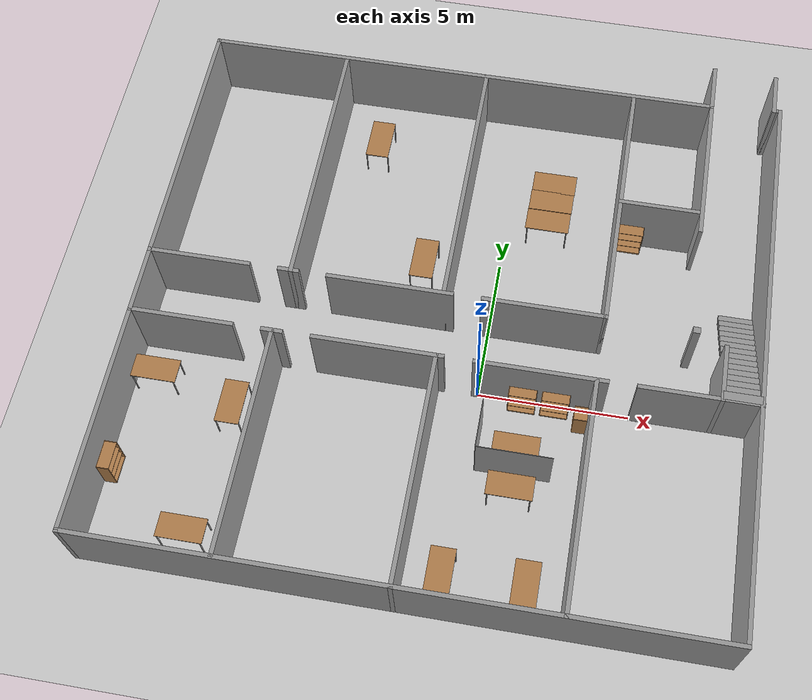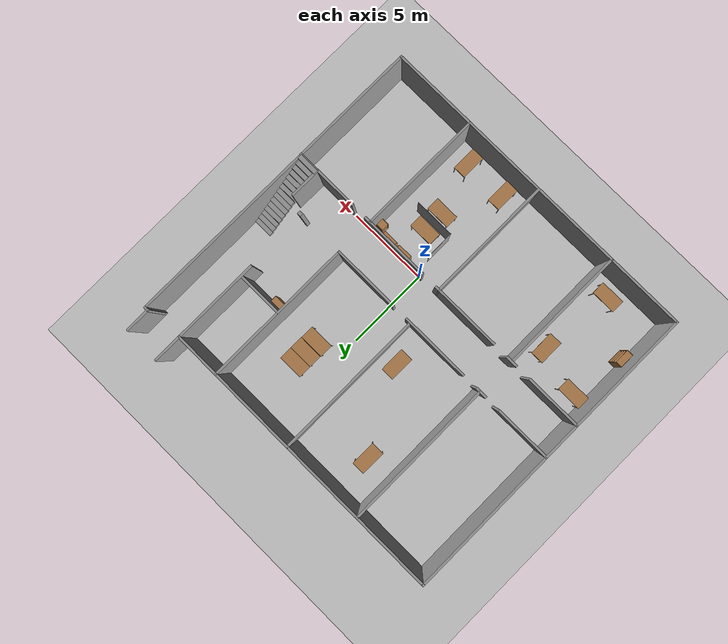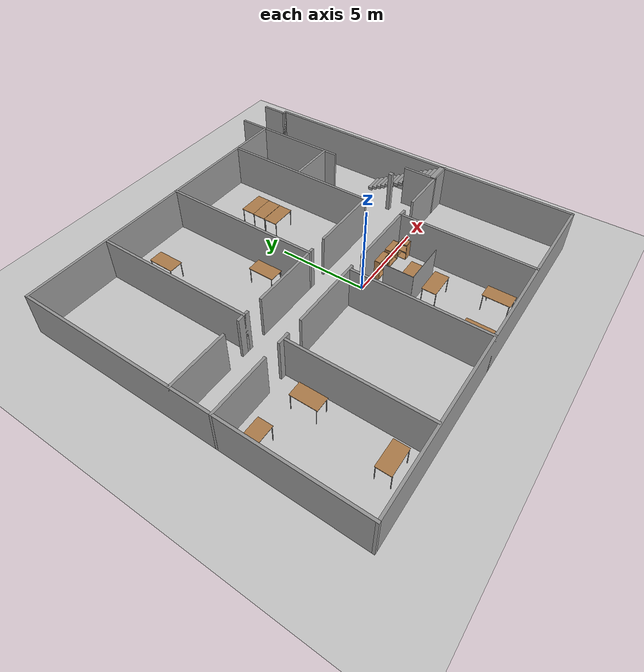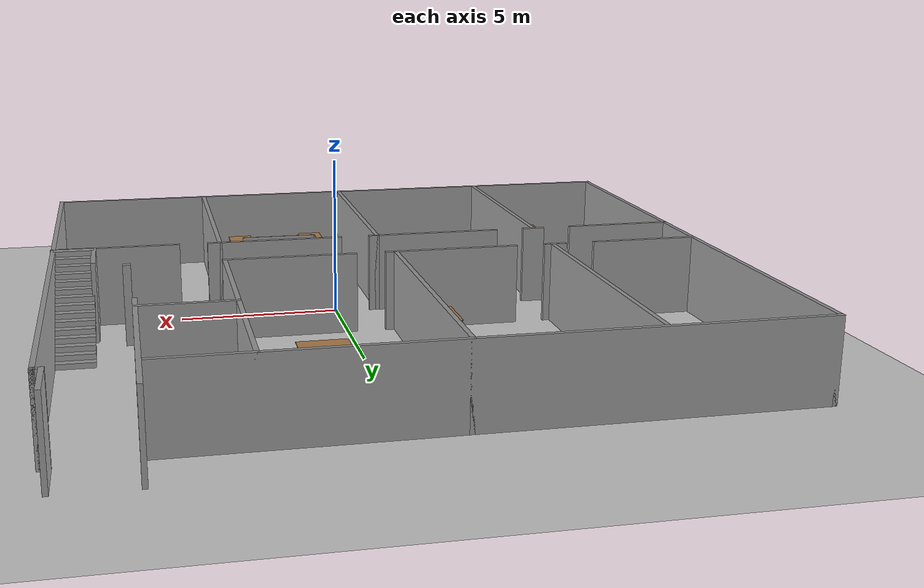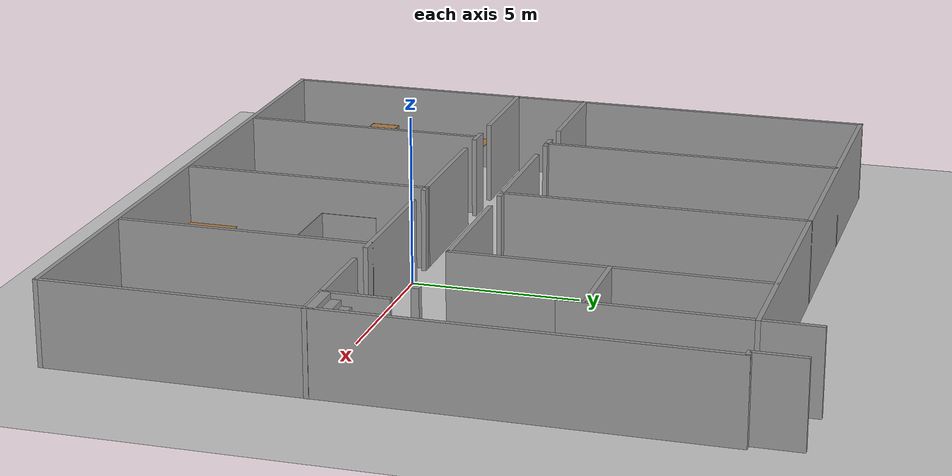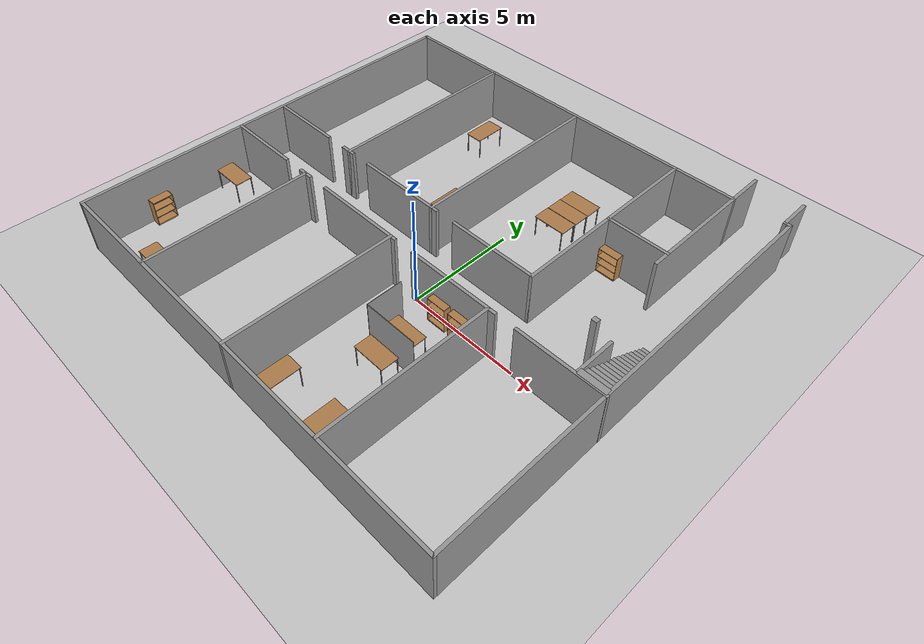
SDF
<sdf version="1.4">
 <world name="default">
  <light name="sun" type="directional">
   <pose>0 0 10 0 -0 0</pose>
   <diffuse>0.8 0.8 0.8 1</diffuse>
   <specular>0.2 0.2 0.2 1</specular>
   <attenuation>
    <range>1000</range>
    <constant>0.9</constant>
    <linear>0.01</linear>
    <quadratic>0.001</quadratic>
   </attenuation>
   <direction>0.5 0.1 -0.9</direction>
  </light>
  <model name="ground_plane">
   <static>1</static>
   <link name="link">
    <collision name="collision">
     <geometry><plane><normal>0 0 1</normal><size>100 100</size></plane></geometry>
     <surface><friction><ode><mu>100</mu><mu2>50</mu2></ode></friction></surface>
    </collision>
    <visual name="visual">
     <cast_shadows>0</cast_shadows>
     <geometry><plane><normal>0 0 1</normal><size>100 100</size></plane></geometry>
     <material>
      <script><uri>file://media/materials/scripts/gazebo.material</uri><name>Gazebo/Grey</name></script>
     </material>
    </visual>
    <velocity_decay><linear>0</linear><angular>0</angular></velocity_decay>
   </link>
  </model>
  <physics type="ode">
   <max_step_size>0.001</max_step_size>
   <real_time_factor>1</real_time_factor>
   <real_time_update_rate>1000</real_time_update_rate>
   <gravity>0 0 -9.8</gravity>
  </physics>
  <scene><ambient>0.4 0.4 0.4 1</ambient><background>0.7 0.7 0.7 1</background><shadows>1</shadows></scene>
  <model name="teknopark">
   <link name="Stairs_0">
    <visual name="Stairs_0_Visual_0">
     <pose>8.265 4.12932 0.083333 0 -0 0</pose>
     <geometry><box><size>1.23 0.284782 0.166668</size></box></geometry>
     <material>
      <script><uri>file://media/materials/scripts/gazebo.material</uri><name>Gazebo/Grey</name></script>
     </material>
    </visual>
    <collision name="Stairs_0_Collision_0">
     <geometry><box><size>1.23 0.284782 0.166668</size></box></geometry>
     <pose>8.265 4.12932 0.083333 0 -0 0</pose>
    </collision>
    <visual name="Stairs_0_Visual_1">
     <pose>8.265 3.84454 0.25 0 -0 0</pose>
     <geometry><box><size>1.23 0.284782 0.166668</size></box></geometry>
     <material>
      <script><uri>file://media/materials/scripts/gazebo.material</uri><name>Gazebo/Grey</name></script>
     </material>
    </visual>
    <collision name="Stairs_0_Collision_1">
     <geometry><box><size>1.23 0.284782 0.166668</size></box></geometry>
     <pose>8.265 3.84454 0.25 0 -0 0</pose>
    </collision>
    <visual name="Stairs_0_Visual_2">
     <pose>8.265 3.55976 0.416667 0 -0 0</pose>
     <geometry><box><size>1.23 0.284782 0.166668</size></box></geometry>
     <material>
      <script><uri>file://media/materials/scripts/gazebo.material</uri><name>Gazebo/Grey</name></script>
     </material>
    </visual>
    <collision name="Stairs_0_Collision_2">
     <geometry><box><size>1.23 0.284782 0.166668</size></box></geometry>
     <pose>8.265 3.55976 0.416667 0 -0 0</pose>
    </collision>
    <visual name="Stairs_0_Visual_3">
     <pose>8.265 3.27498 0.583333 0 -0 0</pose>
     <geometry><box><size>1.23 0.284782 0.166668</size></box></geometry>
     <material>
      <script><uri>file://media/materials/scripts/gazebo.material</uri><name>Gazebo/Grey</name></script>
     </material>
    </visual>
    <collision name="Stairs_0_Collision_3">
     <geometry><box><size>1.23 0.284782 0.166668</size></box></geometry>
     <pose>8.265 3.27498 0.583333 0 -0 0</pose>
    </collision>
    <visual name="Stairs_0_Visual_4">
     <pose>8.265 2.9902 0.75 0 -0 0</pose>
     <geometry><box><size>1.23 0.284782 0.166668</size></box></geometry>
     <material>
      <script><uri>file://media/materials/scripts/gazebo.material</uri><name>Gazebo/Grey</name></script>
     </material>
    </visual>
    <collision name="Stairs_0_Collision_4">
     <geometry><box><size>1.23 0.284782 0.166668</size></box></geometry>
     <pose>8.265 2.9902 0.75 0 -0 0</pose>
    </collision>
    <visual name="Stairs_0_Visual_5">
     <pose>8.265 2.70542 0.916667 0 -0 0</pose>
     <geometry><box><size>1.23 0.284782 0.166668</size></box></geometry>
     <material>
      <script><uri>file://media/materials/scripts/gazebo.material</uri><name>Gazebo/Grey</name></script>
     </material>
    </visual>
    <collision name="Stairs_0_Collision_5">
     <geometry><box><size>1.23 0.284782 0.166668</size></box></geometry>
     <pose>8.265 2.70542 0.916667 0 -0 0</pose>
    </collision>
    <visual name="Stairs_0_Visual_6">
     <pose>8.265 2.42064 1.08333 0 -0 0</pose>
     <geometry><box><size>1.23 0.284782 0.166668</size></box></geometry>
     <material>
      <script><uri>file://media/materials/scripts/gazebo.material</uri><name>Gazebo/Grey</name></script>
     </material>
    </visual>
    <collision name="Stairs_0_Collision_6">
     <geometry><box><size>1.23 0.284782 0.166668</size></box></geometry>
     <pose>8.265 2.42064 1.08333 0 -0 0</pose>
    </collision>
    <visual name="Stairs_0_Visual_7">
     <pose>8.265 2.13586 1.25 0 -0 0</pose>
     <geometry><box><size>1.23 0.284782 0.166668</size></box></geometry>
     <material>
      <script><uri>file://media/materials/scripts/gazebo.material</uri><name>Gazebo/Grey</name></script>
     </material>
    </visual>
    <collision name="Stairs_0_Collision_7">
     <geometry><box><size>1.23 0.284782 0.166668</size></box></geometry>
     <pose>8.265 2.13586 1.25 0 -0 0</pose>
    </collision>
    <visual name="Stairs_0_Visual_8">
     <pose>8.265 1.85108 1.41667 0 -0 0</pose>
     <geometry><box><size>1.23 0.284782 0.166668</size></box></geometry>
     <material>
      <script><uri>file://media/materials/scripts/gazebo.material</uri><name>Gazebo/Grey</name></script>
     </material>
    </visual>
    <collision name="Stairs_0_Collision_8">
     <geometry><box><size>1.23 0.284782 0.166668</size></box></geometry>
     <pose>8.265 1.85108 1.41667 0 -0 0</pose>
    </collision>
    <visual name="Stairs_0_Visual_9">
     <pose>8.265 1.56629 1.58333 0 -0 0</pose>
     <geometry><box><size>1.23 0.284782 0.166668</size></box></geometry>
     <material>
      <script><uri>file://media/materials/scripts/gazebo.material</uri><name>Gazebo/Grey</name></script>
     </material>
    </visual>
    <collision name="Stairs_0_Collision_9">
     <geometry><box><size>1.23 0.284782 0.166668</size></box></geometry>
     <pose>8.265 1.56629 1.58333 0 -0 0</pose>
    </collision>
    <visual name="Stairs_0_Visual_10">
     <pose>8.265 1.28151 1.75 0 -0 0</pose>
     <geometry><box><size>1.23 0.284782 0.166668</size></box></geometry>
     <material>
      <script><uri>file://media/materials/scripts/gazebo.material</uri><name>Gazebo/Grey</name></script>
     </material>
    </visual>
    <collision name="Stairs_0_Collision_10">
     <geometry><box><size>1.23 0.284782 0.166668</size></box></geometry>
     <pose>8.265 1.28151 1.75 0 -0 0</pose>
    </collision>
    <visual name="Stairs_0_Visual_11">
     <pose>8.265 0.996734 1.91667 0 -0 0</pose>
     <geometry><box><size>1.23 0.284782 0.166668</size></box></geometry>
     <material>
      <script><uri>file://media/materials/scripts/gazebo.material</uri><name>Gazebo/Grey</name></script>
     </material>
    </visual>
    <collision name="Stairs_0_Collision_11">
     <geometry><box><size>1.23 0.284782 0.166668</size></box></geometry>
     <pose>8.265 0.996734 1.91667 0 -0 0</pose>
    </collision>
    <visual name="Stairs_0_Visual_12">
     <pose>8.265 0.711953 2.08333 0 -0 0</pose>
     <geometry><box><size>1.23 0.284782 0.166668</size></box></geometry>
     <material>
      <script><uri>file://media/materials/scripts/gazebo.material</uri><name>Gazebo/Grey</name></script>
     </material>
    </visual>
    <collision name="Stairs_0_Collision_12">
     <geometry><box><size>1.23 0.284782 0.166668</size></box></geometry>
     <pose>8.265 0.711953 2.08333 0 -0 0</pose>
    </collision>
    <visual name="Stairs_0_Visual_13">
     <pose>8.265 0.427173 2.25 0 -0 0</pose>
     <geometry><box><size>1.23 0.284782 0.166668</size></box></geometry>
     <material>
      <script><uri>file://media/materials/scripts/gazebo.material</uri><name>Gazebo/Grey</name></script>
     </material>
    </visual>
    <collision name="Stairs_0_Collision_13">
     <geometry><box><size>1.23 0.284782 0.166668</size></box></geometry>
     <pose>8.265 0.427173 2.25 0 -0 0</pose>
    </collision>
    <visual name="Stairs_0_Visual_14">
     <pose>8.265 0.142392 2.41667 0 -0 0</pose>
     <geometry><box><size>1.23 0.284782 0.166668</size></box></geometry>
     <material>
      <script><uri>file://media/materials/scripts/gazebo.material</uri><name>Gazebo/Grey</name></script>
     </material>
    </visual>
    <collision name="Stairs_0_Collision_14">
     <geometry><box><size>1.23 0.284782 0.166668</size></box></geometry>
     <pose>8.265 0.142392 2.41667 0 -0 0</pose>
    </collision>
    <velocity_decay><linear>0</linear><angular>0</angular></velocity_decay>
   </link>
   <link name="Wall_0">
    <collision name="Wall_0_Collision">
     <geometry><box><size>1.57 0.14 2.5</size></box></geometry>
     <pose>0 0 1.25 0 -0 0</pose>
    </collision>
    <visual name="Wall_0_Visual">
     <pose>0 0 1.25 0 -0 0</pose>
     <geometry><box><size>1.57 0.14 2.5</size></box></geometry>
     <material>
      <script><uri>file://media/materials/scripts/gazebo.material</uri><name>Gazebo/Grey</name></script>
     </material>
    </visual>
    <velocity_decay><linear>0</linear><angular>0</angular></velocity_decay>
    <pose>8.67 12.175 0 0 -0 1.5708</pose>
   </link>
   <link name="Wall_10">
    <collision name="Wall_10_Collision">
     <geometry><box><size>3.48 0.14 2.5</size></box></geometry>
     <pose>0 0 1.25 0 -0 0</pose>
    </collision>
    <visual name="Wall_10_Visual">
     <pose>0 0 1.25 0 -0 0</pose>
     <geometry><box><size>3.48 0.14 2.5</size></box></geometry>
     <material>
      <script><uri>file://media/materials/scripts/gazebo.material</uri><name>Gazebo/Grey</name></script>
     </material>
    </visual>
    <velocity_decay><linear>0</linear><angular>0</angular></velocity_decay>
    <pose>-9.69 0 0 0 -0 0</pose>
   </link>
   <link name="Wall_12">
    <collision name="Wall_12_Collision">
     <geometry><box><size>0.72 0.14 2.5</size></box></geometry>
     <pose>0 0 1.25 0 -0 0</pose>
    </collision>
    <visual name="Wall_12_Visual">
     <pose>0 0 1.25 0 -0 0</pose>
     <geometry><box><size>0.72 0.14 2.5</size></box></geometry>
     <material>
      <script><uri>file://media/materials/scripts/gazebo.material</uri><name>Gazebo/Grey</name></script>
     </material>
    </visual>
    <velocity_decay><linear>0</linear><angular>0</angular></velocity_decay>
    <pose>-6.69 0 0 0 -0 0</pose>
   </link>
   <link name="Wall_16">
    <collision name="Wall_16_Collision">
     <geometry><box><size>4.33 0.14 2.5</size></box></geometry>
     <pose>0 0 1.25 0 -0 0</pose>
    </collision>
    <visual name="Wall_16_Visual">
     <pose>0 0 1.25 0 -0 0</pose>
     <geometry><box><size>4.33 0.14 2.5</size></box></geometry>
     <material>
      <script><uri>file://media/materials/scripts/gazebo.material</uri><name>Gazebo/Grey</name></script>
     </material>
    </visual>
    <velocity_decay><linear>0</linear><angular>0</angular></velocity_decay>
    <pose>-3.265 0 0 0 -0 0</pose>
   </link>
   <link name="Wall_18">
    <collision name="Wall_18_Collision">
     <geometry><box><size>7.561 0.14 2.5</size></box></geometry>
     <pose>0 0 1.25 0 -0 0</pose>
    </collision>
    <visual name="Wall_18_Visual">
     <pose>0 0 1.25 0 -0 0</pose>
     <geometry><box><size>7.561 0.14 2.5</size></box></geometry>
     <material>
      <script><uri>file://media/materials/scripts/gazebo.material</uri><name>Gazebo/Grey</name></script>
     </material>
    </visual>
    <velocity_decay><linear>0</linear><angular>0</angular></velocity_decay>
    <pose>-6.687 -3.7695 0 0 0 -1.5708</pose>
   </link>
   <link name="Wall_2">
    <collision name="Wall_2_Collision">
     <geometry><box><size>0.35 0.14 2.5</size></box></geometry>
     <pose>0 0 1.25 0 -0 0</pose>
    </collision>
    <visual name="Wall_2_Visual">
     <pose>0 0 1.25 0 -0 0</pose>
     <geometry><box><size>0.35 0.14 2.5</size></box></geometry>
     <material>
      <script><uri>file://media/materials/scripts/gazebo.material</uri><name>Gazebo/Grey</name></script>
     </material>
    </visual>
    <velocity_decay><linear>0</linear><angular>0</angular></velocity_decay>
    <pose>8.775 11.46 0 0 -0 0</pose>
   </link>
   <link name="Wall_22">
    <collision name="Wall_22_Collision">
     <geometry><box><size>4.32 0.14 2.5</size></box></geometry>
     <pose>0 0 1.25 0 -0 0</pose>
    </collision>
    <visual name="Wall_22_Visual">
     <pose>0 0 1.25 0 -0 0</pose>
     <geometry><box><size>4.32 0.14 2.5</size></box></geometry>
     <material>
      <script><uri>file://media/materials/scripts/gazebo.material</uri><name>Gazebo/Grey</name></script>
     </material>
    </visual>
    <velocity_decay><linear>0</linear><angular>0</angular></velocity_decay>
    <pose>1.96 0 0 0 -0 0</pose>
   </link>
   <link name="Wall_24">
    <collision name="Wall_24_Collision">
     <geometry><box><size>3.971 0.14 2.5</size></box></geometry>
     <pose>0 0 1.25 0 -0 0</pose>
    </collision>
    <visual name="Wall_24_Visual">
     <pose>0 0 1.25 0 -0 0</pose>
     <geometry><box><size>3.971 0.14 2.5</size></box></geometry>
     <material>
      <script><uri>file://media/materials/scripts/gazebo.material</uri><name>Gazebo/Grey</name></script>
     </material>
    </visual>
    <velocity_decay><linear>0</linear><angular>0</angular></velocity_decay>
    <pose>6.9785 0 0 0 -0 0</pose>
   </link>
   <link name="Wall_26">
    <collision name="Wall_26_Collision">
     <geometry><box><size>1.97 0.14 2.5</size></box></geometry>
     <pose>0 0 1.25 0 -0 0</pose>
    </collision>
    <visual name="Wall_26_Visual">
     <pose>0 0 1.25 0 -0 0</pose>
     <geometry><box><size>1.97 0.14 2.5</size></box></geometry>
     <material>
      <script><uri>file://media/materials/scripts/gazebo.material</uri><name>Gazebo/Grey</name></script>
     </material>
    </visual>
    <velocity_decay><linear>0</linear><angular>0</angular></velocity_decay>
    <pose>7.65 0.915 0 0 -0 1.5708</pose>
   </link>
   <link name="Wall_28">
    <collision name="Wall_28_Collision">
     <geometry><box><size>7.67 0.14 2.5</size></box></geometry>
     <pose>0 0 1.25 0 -0 0</pose>
    </collision>
    <visual name="Wall_28_Visual">
     <pose>0 0 1.25 0 -0 0</pose>
     <geometry><box><size>7.67 0.14 2.5</size></box></geometry>
     <material>
      <script><uri>file://media/materials/scripts/gazebo.material</uri><name>Gazebo/Grey</name></script>
     </material>
    </visual>
    <velocity_decay><linear>0</linear><angular>0</angular></velocity_decay>
    <pose>-1.37 -3.765 0 0 0 -1.5708</pose>
   </link>
   <link name="Wall_30">
    <collision name="Wall_30_Collision">
     <geometry><box><size>7.67 0.14 2.5</size></box></geometry>
     <pose>0 0 1.25 0 -0 0</pose>
    </collision>
    <visual name="Wall_30_Visual">
     <pose>0 0 1.25 0 -0 0</pose>
     <geometry><box><size>7.67 0.14 2.5</size></box></geometry>
     <material>
      <script><uri>file://media/materials/scripts/gazebo.material</uri><name>Gazebo/Grey</name></script>
     </material>
    </visual>
    <velocity_decay><linear>0</linear><angular>0</angular></velocity_decay>
    <pose>3.73 -3.765 0 0 0 -1.5708</pose>
   </link>
   <link name="Wall_32">
    <collision name="Wall_32_Collision">
     <geometry><box><size>18 0.14 2.5</size></box></geometry>
     <pose>0 0 1.25 0 -0 0</pose>
    </collision>
    <visual name="Wall_32_Visual">
     <pose>0 0 1.25 0 -0 0</pose>
     <geometry><box><size>18 0.14 2.5</size></box></geometry>
     <material>
      <script><uri>file://media/materials/scripts/gazebo.material</uri><name>Gazebo/Grey</name></script>
     </material>
    </visual>
    <velocity_decay><linear>0</linear><angular>0</angular></velocity_decay>
    <pose>-2.43 11.28 0 0 -0 0</pose>
   </link>
   <link name="Wall_34">
    <collision name="Wall_34_Collision">
     <geometry><box><size>3.467 0.14 2.5</size></box></geometry>
     <pose>0 0 1.25 0 -0 0</pose>
    </collision>
    <visual name="Wall_34_Visual">
     <pose>0 0 1.25 0 -0 0</pose>
     <geometry><box><size>3.467 0.14 2.5</size></box></geometry>
     <material>
      <script><uri>file://media/materials/scripts/gazebo.material</uri><name>Gazebo/Grey</name></script>
     </material>
    </visual>
    <velocity_decay><linear>0</linear><angular>0</angular></velocity_decay>
    <pose>-9.6965 2.273 0 0 -0 0</pose>
   </link>
   <link name="Wall_38">
    <collision name="Wall_38_Collision">
     <geometry><box><size>0.72 0.14 2.5</size></box></geometry>
     <pose>0 0 1.25 0 -0 0</pose>
    </collision>
    <visual name="Wall_38_Visual">
     <pose>0 0 1.25 0 -0 0</pose>
     <geometry><box><size>0.72 0.14 2.5</size></box></geometry>
     <material>
      <script><uri>file://media/materials/scripts/gazebo.material</uri><name>Gazebo/Grey</name></script>
     </material>
    </visual>
    <velocity_decay><linear>0</linear><angular>0</angular></velocity_decay>
    <pose>-6.68 2.273 0 0 -0 0</pose>
   </link>
   <link name="Wall_4">
    <collision name="Wall_4_Collision">
     <geometry><box><size>19.13 0.14 2.5</size></box></geometry>
     <pose>0 0 1.25 0 -0 0</pose>
    </collision>
    <visual name="Wall_4_Visual">
     <pose>0 0 1.25 0 -0 0</pose>
     <geometry><box><size>19.13 0.14 2.5</size></box></geometry>
     <material>
      <script><uri>file://media/materials/scripts/gazebo.material</uri><name>Gazebo/Grey</name></script>
     </material>
    </visual>
    <velocity_decay><linear>0</linear><angular>0</angular></velocity_decay>
    <pose>8.88 1.965 0 0 0 -1.5708</pose>
   </link>
   <link name="Wall_40">
    <collision name="Wall_40_Collision">
     <geometry><box><size>4.23 0.14 2.5</size></box></geometry>
     <pose>0 0 1.25 0 -0 0</pose>
    </collision>
    <visual name="Wall_40_Visual">
     <pose>0 0 1.25 0 -0 0</pose>
     <geometry><box><size>4.23 0.14 2.5</size></box></geometry>
     <material>
      <script><uri>file://media/materials/scripts/gazebo.material</uri><name>Gazebo/Grey</name></script>
     </material>
    </visual>
    <velocity_decay><linear>0</linear><angular>0</angular></velocity_decay>
    <pose>-3.305 2.273 0 0 -0 0</pose>
   </link>
   <link name="Wall_42">
    <collision name="Wall_42_Collision">
     <geometry><box><size>4.12 0.14 2.5</size></box></geometry>
     <pose>0 0 1.25 0 -0 0</pose>
    </collision>
    <visual name="Wall_42_Visual">
     <pose>0 0 1.25 0 -0 0</pose>
     <geometry><box><size>4.12 0.14 2.5</size></box></geometry>
     <material>
      <script><uri>file://media/materials/scripts/gazebo.material</uri><name>Gazebo/Grey</name></script>
     </material>
    </visual>
    <velocity_decay><linear>0</linear><angular>0</angular></velocity_decay>
    <pose>1.77 2.273 0 0 -0 0</pose>
   </link>
   <link name="Wall_44">
    <collision name="Wall_44_Collision">
     <geometry><box><size>9.147 0.14 2.5</size></box></geometry>
     <pose>0 0 1.25 0 -0 0</pose>
    </collision>
    <visual name="Wall_44_Visual">
     <pose>0 0 1.25 0 -0 0</pose>
     <geometry><box><size>9.147 0.14 2.5</size></box></geometry>
     <material>
      <script><uri>file://media/materials/scripts/gazebo.material</uri><name>Gazebo/Grey</name></script>
     </material>
    </visual>
    <velocity_decay><linear>0</linear><angular>0</angular></velocity_decay>
    <pose>3.76 6.7765 0 0 -0 1.5708</pose>
   </link>
   <link name="Wall_46">
    <collision name="Wall_46_Collision">
     <geometry><box><size>2.88 0.14 2.5</size></box></geometry>
     <pose>0 0 1.25 0 -0 0</pose>
    </collision>
    <visual name="Wall_46_Visual">
     <pose>0 0 1.25 0 -0 0</pose>
     <geometry><box><size>2.88 0.14 2.5</size></box></geometry>
     <material>
      <script><uri>file://media/materials/scripts/gazebo.material</uri><name>Gazebo/Grey</name></script>
     </material>
    </visual>
    <velocity_decay><linear>0</linear><angular>0</angular></velocity_decay>
    <pose>5.13 6.77 0 0 -0 0</pose>
   </link>
   <link name="Wall_48">
    <collision name="Wall_48_Collision">
     <geometry><box><size>7.003 0.14 2.5</size></box></geometry>
     <pose>0 0 1.25 0 -0 0</pose>
    </collision>
    <visual name="Wall_48_Visual">
     <pose>0 0 1.25 0 -0 0</pose>
     <geometry><box><size>7.003 0.14 2.5</size></box></geometry>
     <material>
      <script><uri>file://media/materials/scripts/gazebo.material</uri><name>Gazebo/Grey</name></script>
     </material>
    </visual>
    <velocity_decay><linear>0</linear><angular>0</angular></velocity_decay>
    <pose>6.5 9.5015 0 0 -0 1.5708</pose>
   </link>
   <link name="Wall_50">
    <collision name="Wall_50_Collision">
     <geometry><box><size>9.147 0.14 2.5</size></box></geometry>
     <pose>0 0 1.25 0 -0 0</pose>
    </collision>
    <visual name="Wall_50_Visual">
     <pose>0 0 1.25 0 -0 0</pose>
     <geometry><box><size>9.147 0.14 2.5</size></box></geometry>
     <material>
      <script><uri>file://media/materials/scripts/gazebo.material</uri><name>Gazebo/Grey</name></script>
     </material>
    </visual>
    <velocity_decay><linear>0</linear><angular>0</angular></velocity_decay>
    <pose>-6.6 6.7765 0 0 -0 1.5708</pose>
   </link>
   <link name="Wall_52">
    <collision name="Wall_52_Collision">
     <geometry><box><size>9.147 0.14 2.5</size></box></geometry>
     <pose>0 0 1.25 0 -0 0</pose>
    </collision>
    <visual name="Wall_52_Visual">
     <pose>0 0 1.25 0 -0 0</pose>
     <geometry><box><size>9.147 0.14 2.5</size></box></geometry>
     <material>
      <script><uri>file://media/materials/scripts/gazebo.material</uri><name>Gazebo/Grey</name></script>
     </material>
    </visual>
    <velocity_decay><linear>0</linear><angular>0</angular></velocity_decay>
    <pose>-1.52 6.7765 0 0 -0 1.5708</pose>
   </link>
   <link name="Wall_6">
    <collision name="Wall_6_Collision">
     <geometry><box><size>20.38 0.14 2.5</size></box></geometry>
     <pose>0 0 1.25 0 -0 0</pose>
    </collision>
    <visual name="Wall_6_Visual">
     <pose>0 0 1.25 0 -0 0</pose>
     <geometry><box><size>20.38 0.14 2.5</size></box></geometry>
     <material>
      <script><uri>file://media/materials/scripts/gazebo.material</uri><name>Gazebo/Grey</name></script>
     </material>
    </visual>
    <velocity_decay><linear>0</linear><angular>0</angular></velocity_decay>
    <pose>-1.24 -7.53 0 0 -0 3.14159</pose>
   </link>
   <link name="Wall_8">
    <collision name="Wall_8_Collision">
     <geometry><box><size>18.95 0.14 2.5</size></box></geometry>
     <pose>0 0 1.25 0 -0 0</pose>
    </collision>
    <visual name="Wall_8_Visual">
     <pose>0 0 1.25 0 -0 0</pose>
     <geometry><box><size>18.95 0.14 2.5</size></box></geometry>
     <material>
      <script><uri>file://media/materials/scripts/gazebo.material</uri><name>Gazebo/Grey</name></script>
     </material>
    </visual>
    <velocity_decay><linear>0</linear><angular>0</angular></velocity_decay>
    <pose>-11.36 1.875 0 0 -0 1.5708</pose>
   </link>
   <static>1</static>
  </model>
  <model name="teknopark_ik2">
   <link name="Wall_3">
    <collision name="Wall_3_Collision">
     <geometry><box><size>1.66 0.02 2</size></box></geometry>
     <pose>0 0 1 0 -0 0</pose>
    </collision>
    <visual name="Wall_3_Visual">
     <pose>0 0 1 0 -0 0</pose>
     <geometry><box><size>1.66 0.02 2</size></box></geometry>
     <material>
      <script><uri>file://media/materials/scripts/gazebo.material</uri><name>Gazebo/Grey</name></script>
     </material>
    </visual>
    <velocity_decay><linear>0</linear><angular>0</angular></velocity_decay>
    <pose>0.312 -1.818 0 0 -0 1.5708</pose>
   </link>
   <link name="Wall_9">
    <collision name="Wall_9_Collision">
     <geometry><box><size>2.45 0.02 2</size></box></geometry>
     <pose>0 0 1 0 -0 0</pose>
    </collision>
    <visual name="Wall_9_Visual">
     <pose>0 0 1 0 -0 0</pose>
     <geometry><box><size>2.45 0.02 2</size></box></geometry>
     <material>
      <script><uri>file://media/materials/scripts/gazebo.material</uri><name>Gazebo/Grey</name></script>
     </material>
    </visual>
    <velocity_decay><linear>0</linear><angular>0</angular></velocity_decay>
    <pose>1.528 -2.637 0 0 -0 0</pose>
   </link>
   <static>1</static>
  </model>
  <model name="table">
   <static>1</static>
   <link name="link">
    <collision name="surface">
     <pose>0 0 1 0 -0 0</pose>
     <geometry><box><size>1.5 0.8 0.03</size></box></geometry>
    </collision>
    <visual name="visual1">
     <pose>0 0 1 0 -0 0</pose>
     <geometry><box><size>1.5 0.8 0.03</size></box></geometry>
     <material>
      <script><uri>file://media/materials/scripts/gazebo.material</uri><name>Gazebo/Wood</name></script>
     </material>
    </visual>
    <collision name="front_left_leg">
     <pose>0.68 0.38 0.5 0 -0 0</pose>
     <geometry><cylinder><radius>0.02</radius><length>1</length></cylinder></geometry>
    </collision>
    <visual name="front_left_leg">
     <pose>0.68 0.38 0.5 0 -0 0</pose>
     <geometry><cylinder><radius>0.02</radius><length>1</length></cylinder></geometry>
     <material>
      <script><uri>file://media/materials/scripts/gazebo.material</uri><name>Gazebo/Grey</name></script>
     </material>
    </visual>
    <collision name="front_right_leg">
     <pose>0.68 -0.38 0.5 0 -0 0</pose>
     <geometry><cylinder><radius>0.02</radius><length>1</length></cylinder></geometry>
    </collision>
    <visual name="front_right_leg">
     <pose>0.68 -0.38 0.5 0 -0 0</pose>
     <geometry><cylinder><radius>0.02</radius><length>1</length></cylinder></geometry>
     <material>
      <script><uri>file://media/materials/scripts/gazebo.material</uri><name>Gazebo/Grey</name></script>
     </material>
    </visual>
    <collision name="back_right_leg">
     <pose>-0.68 -0.38 0.5 0 -0 0</pose>
     <geometry><cylinder><radius>0.02</radius><length>1</length></cylinder></geometry>
    </collision>
    <visual name="back_right_leg">
     <pose>-0.68 -0.38 0.5 0 -0 0</pose>
     <geometry><cylinder><radius>0.02</radius><length>1</length></cylinder></geometry>
     <material>
      <script><uri>file://media/materials/scripts/gazebo.material</uri><name>Gazebo/Grey</name></script>
     </material>
    </visual>
    <collision name="back_left_leg">
     <pose>-0.68 0.38 0.5 0 -0 0</pose>
     <geometry><cylinder><radius>0.02</radius><length>1</length></cylinder></geometry>
    </collision>
    <visual name="back_left_leg">
     <pose>-0.68 0.38 0.5 0 -0 0</pose>
     <geometry><cylinder><radius>0.02</radius><length>1</length></cylinder></geometry>
     <material>
      <script><uri>file://media/materials/scripts/gazebo.material</uri><name>Gazebo/Grey</name></script>
     </material>
    </visual>
    <velocity_decay><linear>0</linear><angular>0</angular></velocity_decay>
   </link>
   <pose>2.471 -6.373 0 0 -0 1.57</pose>
  </model>
  <model name="table_0">
   <static>1</static>
   <link name="link">
    <collision name="surface">
     <pose>0 0 1 0 -0 0</pose>
     <geometry><box><size>1.5 0.8 0.03</size></box></geometry>
    </collision>
    <visual name="visual1">
     <pose>0 0 1 0 -0 0</pose>
     <geometry><box><size>1.5 0.8 0.03</size></box></geometry>
     <material>
      <script><uri>file://media/materials/scripts/gazebo.material</uri><name>Gazebo/Wood</name></script>
     </material>
    </visual>
    <collision name="front_left_leg">
     <pose>0.68 0.38 0.5 0 -0 0</pose>
     <geometry><cylinder><radius>0.02</radius><length>1</length></cylinder></geometry>
    </collision>
    <visual name="front_left_leg">
     <pose>0.68 0.38 0.5 0 -0 0</pose>
     <geometry><cylinder><radius>0.02</radius><length>1</length></cylinder></geometry>
     <material>
      <script><uri>file://media/materials/scripts/gazebo.material</uri><name>Gazebo/Grey</name></script>
     </material>
    </visual>
    <collision name="front_right_leg">
     <pose>0.68 -0.38 0.5 0 -0 0</pose>
     <geometry><cylinder><radius>0.02</radius><length>1</length></cylinder></geometry>
    </collision>
    <visual name="front_right_leg">
     <pose>0.68 -0.38 0.5 0 -0 0</pose>
     <geometry><cylinder><radius>0.02</radius><length>1</length></cylinder></geometry>
     <material>
      <script><uri>file://media/materials/scripts/gazebo.material</uri><name>Gazebo/Grey</name></script>
     </material>
    </visual>
    <collision name="back_right_leg">
     <pose>-0.68 -0.38 0.5 0 -0 0</pose>
     <geometry><cylinder><radius>0.02</radius><length>1</length></cylinder></geometry>
    </collision>
    <visual name="back_right_leg">
     <pose>-0.68 -0.38 0.5 0 -0 0</pose>
     <geometry><cylinder><radius>0.02</radius><length>1</length></cylinder></geometry>
     <material>
      <script><uri>file://media/materials/scripts/gazebo.material</uri><name>Gazebo/Grey</name></script>
     </material>
    </visual>
    <collision name="back_left_leg">
     <pose>-0.68 0.38 0.5 0 -0 0</pose>
     <geometry><cylinder><radius>0.02</radius><length>1</length></cylinder></geometry>
    </collision>
    <visual name="back_left_leg">
     <pose>-0.68 0.38 0.5 0 -0 0</pose>
     <geometry><cylinder><radius>0.02</radius><length>1</length></cylinder></geometry>
     <material>
      <script><uri>file://media/materials/scripts/gazebo.material</uri><name>Gazebo/Grey</name></script>
     </material>
    </visual>
    <velocity_decay><linear>0</linear><angular>0</angular></velocity_decay>
   </link>
   <pose>-0.14 -6.398 0 0 -0 1.57</pose>
  </model>
  <model name="bookshelf">
   <static>1</static>
   <link name="link">
    <inertial><mass>1</mass></inertial>
    <collision name="back">
     <pose>0 0.005 0.6 0 -0 0</pose>
     <geometry><box><size>0.9 0.01 1.2</size></box></geometry>
    </collision>
    <visual name="visual1">
     <pose>0 0.005 0.6 0 -0 0</pose>
     <geometry><box><size>0.9 0.01 1.2</size></box></geometry>
     <material>
      <script><uri>file://media/materials/scripts/gazebo.material</uri><name>Gazebo/Wood</name></script>
     </material>
    </visual>
    <collision name="left_side">
     <pose>0.45 -0.195 0.6 0 -0 0</pose>
     <geometry><box><size>0.02 0.4 1.2</size></box></geometry>
    </collision>
    <visual name="visual2">
     <pose>0.45 -0.195 0.6 0 -0 0</pose>
     <geometry><box><size>0.02 0.4 1.2</size></box></geometry>
     <material>
      <script><uri>file://media/materials/scripts/gazebo.material</uri><name>Gazebo/Wood</name></script>
     </material>
    </visual>
    <collision name="right_side">
     <pose>-0.45 -0.195 0.6 0 -0 0</pose>
     <geometry><box><size>0.02 0.4 1.2</size></box></geometry>
    </collision>
    <visual name="visual3">
     <pose>-0.45 -0.195 0.6 0 -0 0</pose>
     <geometry><box><size>0.02 0.4 1.2</size></box></geometry>
     <material>
      <script><uri>file://media/materials/scripts/gazebo.material</uri><name>Gazebo/Wood</name></script>
     </material>
    </visual>
    <collision name="bottom">
     <pose>0 -0.195 0.03 0 -0 0</pose>
     <geometry><box><size>0.88 0.4 0.06</size></box></geometry>
    </collision>
    <visual name="visual4">
     <pose>0 -0.195 0.03 0 -0 0</pose>
     <geometry><box><size>0.88 0.4 0.06</size></box></geometry>
     <material>
      <script><uri>file://media/materials/scripts/gazebo.material</uri><name>Gazebo/Wood</name></script>
     </material>
    </visual>
    <collision name="top">
     <pose>0 -0.195 1.19 0 -0 0</pose>
     <geometry><box><size>0.88 0.4 0.02</size></box></geometry>
    </collision>
    <visual name="visual5">
     <pose>0 -0.195 1.19 0 -0 0</pose>
     <geometry><box><size>0.88 0.4 0.02</size></box></geometry>
     <material>
      <script><uri>file://media/materials/scripts/gazebo.material</uri><name>Gazebo/Wood</name></script>
     </material>
    </visual>
    <collision name="low_shelf">
     <pose>0 -0.195 0.43 0 -0 0</pose>
     <geometry><box><size>0.88 0.4 0.02</size></box></geometry>
    </collision>
    <visual name="visual6">
     <pose>0 -0.195 0.43 0 -0 0</pose>
     <geometry><box><size>0.88 0.4 0.02</size></box></geometry>
     <material>
      <script><uri>file://media/materials/scripts/gazebo.material</uri><name>Gazebo/Wood</name></script>
     </material>
    </visual>
    <collision name="high_shelf">
     <pose>0 -0.195 0.8 0 -0 0</pose>
     <geometry><box><size>0.88 0.4 0.02</size></box></geometry>
    </collision>
    <visual name="visual7">
     <pose>0 -0.195 0.8 0 -0 0</pose>
     <geometry><box><size>0.88 0.4 0.02</size></box></geometry>
     <material>
      <script><uri>file://media/materials/scripts/gazebo.material</uri><name>Gazebo/Wood</name></script>
     </material>
    </visual>
    <velocity_decay><linear>0</linear><angular>0</angular></velocity_decay>
   </link>
   <pose>4.281 6.73 0 0 -0 0</pose>
  </model>
  <model name="cabinet">
   <static>1</static>
   <link name="cabinet_bottom_plate">
    <inertial>
     <pose>0 0 -1 0 -0 0</pose>
     <inertia><ixx>2.05</ixx><ixy>0</ixy><ixz>0</ixz><iyy>2.05</iyy><iyz>0</iyz><izz>2.05</izz></inertia>
     <mass>25</mass>
    </inertial>
    <collision name="cabinet_bottom_plate_geom">
     <pose>0 0 0.01 0 -0 0</pose>
     <geometry><box><size>0.45 0.45 0.02</size></box></geometry>
    </collision>
    <visual name="cabinet_bottom_plate_geom_visual">
     <pose>0 0 0.01 0 -0 0</pose>
     <geometry><box><size>0.45 0.45 0.02</size></box></geometry>
     <material>
      <script><uri>file://media/materials/scripts/gazebo.material</uri><name>Gazebo/Wood</name></script>
     </material>
    </visual>
    <collision name="cabinet_bottom_plate_geom_cabinet_back_plate">
     <pose>0.235 0 0.51 0 -0 0</pose>
     <geometry><box><size>0.02 0.45 1.02</size></box></geometry>
    </collision>
    <visual name="cabinet_bottom_plate_geom_cabinet_back_plate_visual">
     <pose>0.235 0 0.51 0 -0 0</pose>
     <geometry><box><size>0.02 0.45 1.02</size></box></geometry>
     <material>
      <script><uri>file://media/materials/scripts/gazebo.material</uri><name>Gazebo/Wood</name></script>
     </material>
    </visual>
    <collision name="cabinet_bottom_plate_geom_cabinet_left_plate">
     <pose>0 0.235 0.51 0 -0 0</pose>
     <geometry><box><size>0.45 0.02 1.02</size></box></geometry>
    </collision>
    <visual name="cabinet_bottom_plate_geom_cabinet_left_plate_visual">
     <pose>0 0.235 0.51 0 -0 0</pose>
     <geometry><box><size>0.45 0.02 1.02</size></box></geometry>
     <material>
      <script><uri>file://media/materials/scripts/gazebo.material</uri><name>Gazebo/Wood</name></script>
     </material>
    </visual>
    <collision name="cabinet_bottom_plate_geom_cabinet_middle_plate">
     <pose>0 0 0.51 0 -0 0</pose>
     <geometry><box><size>0.45 0.45 0.02</size></box></geometry>
    </collision>
    <visual name="cabinet_bottom_plate_geom_cabinet_middle_plate_visual">
     <pose>0 0 0.51 0 -0 0</pose>
     <geometry><box><size>0.45 0.45 0.02</size></box></geometry>
     <material>
      <script><uri>file://media/materials/scripts/gazebo.material</uri><name>Gazebo/Wood</name></script>
     </material>
    </visual>
    <collision name="cabinet_bottom_plate_geom_cabinet_right_plate">
     <pose>0 -0.235 0.51 0 -0 0</pose>
     <geometry><box><size>0.45 0.02 1.02</size></box></geometry>
    </collision>
    <visual name="cabinet_bottom_plate_geom_cabinet_right_plate_visual">
     <pose>0 -0.235 0.51 0 -0 0</pose>
     <geometry><box><size>0.45 0.02 1.02</size></box></geometry>
     <material>
      <script><uri>file://media/materials/scripts/gazebo.material</uri><name>Gazebo/Wood</name></script>
     </material>
    </visual>
    <collision name="cabinet_bottom_plate_geom_cabinet_top_plate">
     <pose>0 0 1.01 0 -0 0</pose>
     <geometry><box><size>0.45 0.45 0.02</size></box></geometry>
    </collision>
    <visual name="cabinet_bottom_plate_geom_cabinet_top_plate_visual">
     <pose>0 0 1.01 0 -0 0</pose>
     <geometry><box><size>0.45 0.45 0.02</size></box></geometry>
     <material>
      <script><uri>file://media/materials/scripts/gazebo.material</uri><name>Gazebo/Wood</name></script>
     </material>
    </visual>
    <velocity_decay><linear>0</linear><angular>0</angular></velocity_decay>
   </link>
   <pose>3.443 -0.556 0 0 -0 0</pose>
  </model>
  <model name="table_1">
   <static>1</static>
   <link name="link">
    <collision name="surface">
     <pose>0 0 1 0 -0 0</pose>
     <geometry><box><size>1.5 0.8 0.03</size></box></geometry>
    </collision>
    <visual name="visual1">
     <pose>0 0 1 0 -0 0</pose>
     <geometry><box><size>1.5 0.8 0.03</size></box></geometry>
     <material>
      <script><uri>file://media/materials/scripts/gazebo.material</uri><name>Gazebo/Wood</name></script>
     </material>
    </visual>
    <collision name="front_left_leg">
     <pose>0.68 0.38 0.5 0 -0 0</pose>
     <geometry><cylinder><radius>0.02</radius><length>1</length></cylinder></geometry>
    </collision>
    <visual name="front_left_leg">
     <pose>0.68 0.38 0.5 0 -0 0</pose>
     <geometry><cylinder><radius>0.02</radius><length>1</length></cylinder></geometry>
     <material>
      <script><uri>file://media/materials/scripts/gazebo.material</uri><name>Gazebo/Grey</name></script>
     </material>
    </visual>
    <collision name="front_right_leg">
     <pose>0.68 -0.38 0.5 0 -0 0</pose>
     <geometry><cylinder><radius>0.02</radius><length>1</length></cylinder></geometry>
    </collision>
    <visual name="front_right_leg">
     <pose>0.68 -0.38 0.5 0 -0 0</pose>
     <geometry><cylinder><radius>0.02</radius><length>1</length></cylinder></geometry>
     <material>
      <script><uri>file://media/materials/scripts/gazebo.material</uri><name>Gazebo/Grey</name></script>
     </material>
    </visual>
    <collision name="back_right_leg">
     <pose>-0.68 -0.38 0.5 0 -0 0</pose>
     <geometry><cylinder><radius>0.02</radius><length>1</length></cylinder></geometry>
    </collision>
    <visual name="back_right_leg">
     <pose>-0.68 -0.38 0.5 0 -0 0</pose>
     <geometry><cylinder><radius>0.02</radius><length>1</length></cylinder></geometry>
     <material>
      <script><uri>file://media/materials/scripts/gazebo.material</uri><name>Gazebo/Grey</name></script>
     </material>
    </visual>
    <collision name="back_left_leg">
     <pose>-0.68 0.38 0.5 0 -0 0</pose>
     <geometry><cylinder><radius>0.02</radius><length>1</length></cylinder></geometry>
    </collision>
    <visual name="back_left_leg">
     <pose>-0.68 0.38 0.5 0 -0 0</pose>
     <geometry><cylinder><radius>0.02</radius><length>1</length></cylinder></geometry>
     <material>
      <script><uri>file://media/materials/scripts/gazebo.material</uri><name>Gazebo/Grey</name></script>
     </material>
    </visual>
    <velocity_decay><linear>0</linear><angular>0</angular></velocity_decay>
   </link>
   <pose>1.554 -3.348 0 0 -0 0</pose>
  </model>
  <model name="bookshelf_1">
   <static>1</static>
   <link name="link">
    <inertial><mass>1</mass></inertial>
    <collision name="back">
     <pose>0 0.005 0.6 0 -0 0</pose>
     <geometry><box><size>0.9 0.01 1.2</size></box></geometry>
    </collision>
    <visual name="visual1">
     <pose>0 0.005 0.6 0 -0 0</pose>
     <geometry><box><size>0.9 0.01 1.2</size></box></geometry>
     <material>
      <script><uri>file://media/materials/scripts/gazebo.material</uri><name>Gazebo/Wood</name></script>
     </material>
    </visual>
    <collision name="left_side">
     <pose>0.45 -0.195 0.6 0 -0 0</pose>
     <geometry><box><size>0.02 0.4 1.2</size></box></geometry>
    </collision>
    <visual name="visual2">
     <pose>0.45 -0.195 0.6 0 -0 0</pose>
     <geometry><box><size>0.02 0.4 1.2</size></box></geometry>
     <material>
      <script><uri>file://media/materials/scripts/gazebo.material</uri><name>Gazebo/Wood</name></script>
     </material>
    </visual>
    <collision name="right_side">
     <pose>-0.45 -0.195 0.6 0 -0 0</pose>
     <geometry><box><size>0.02 0.4 1.2</size></box></geometry>
    </collision>
    <visual name="visual3">
     <pose>-0.45 -0.195 0.6 0 -0 0</pose>
     <geometry><box><size>0.02 0.4 1.2</size></box></geometry>
     <material>
      <script><uri>file://media/materials/scripts/gazebo.material</uri><name>Gazebo/Wood</name></script>
     </material>
    </visual>
    <collision name="bottom">
     <pose>0 -0.195 0.03 0 -0 0</pose>
     <geometry><box><size>0.88 0.4 0.06</size></box></geometry>
    </collision>
    <visual name="visual4">
     <pose>0 -0.195 0.03 0 -0 0</pose>
     <geometry><box><size>0.88 0.4 0.06</size></box></geometry>
     <material>
      <script><uri>file://media/materials/scripts/gazebo.material</uri><name>Gazebo/Wood</name></script>
     </material>
    </visual>
    <collision name="top">
     <pose>0 -0.195 1.19 0 -0 0</pose>
     <geometry><box><size>0.88 0.4 0.02</size></box></geometry>
    </collision>
    <visual name="visual5">
     <pose>0 -0.195 1.19 0 -0 0</pose>
     <geometry><box><size>0.88 0.4 0.02</size></box></geometry>
     <material>
      <script><uri>file://media/materials/scripts/gazebo.material</uri><name>Gazebo/Wood</name></script>
     </material>
    </visual>
    <collision name="low_shelf">
     <pose>0 -0.195 0.43 0 -0 0</pose>
     <geometry><box><size>0.88 0.4 0.02</size></box></geometry>
    </collision>
    <visual name="visual6">
     <pose>0 -0.195 0.43 0 -0 0</pose>
     <geometry><box><size>0.88 0.4 0.02</size></box></geometry>
     <material>
      <script><uri>file://media/materials/scripts/gazebo.material</uri><name>Gazebo/Wood</name></script>
     </material>
    </visual>
    <collision name="high_shelf">
     <pose>0 -0.195 0.8 0 -0 0</pose>
     <geometry><box><size>0.88 0.4 0.02</size></box></geometry>
    </collision>
    <visual name="visual7">
     <pose>0 -0.195 0.8 0 -0 0</pose>
     <geometry><box><size>0.88 0.4 0.02</size></box></geometry>
     <material>
      <script><uri>file://media/materials/scripts/gazebo.material</uri><name>Gazebo/Wood</name></script>
     </material>
    </visual>
    <velocity_decay><linear>0</linear><angular>0</angular></velocity_decay>
   </link>
   <pose>2.57231 0 0 0 -0 0</pose>
  </model>
  <model name="bookshelf_2">
   <static>1</static>
   <link name="link">
    <inertial><mass>1</mass></inertial>
    <collision name="back">
     <pose>0 0.005 0.6 0 -0 0</pose>
     <geometry><box><size>0.9 0.01 1.2</size></box></geometry>
    </collision>
    <visual name="visual1">
     <pose>0 0.005 0.6 0 -0 0</pose>
     <geometry><box><size>0.9 0.01 1.2</size></box></geometry>
     <material>
      <script><uri>file://media/materials/scripts/gazebo.material</uri><name>Gazebo/Wood</name></script>
     </material>
    </visual>
    <collision name="left_side">
     <pose>0.45 -0.195 0.6 0 -0 0</pose>
     <geometry><box><size>0.02 0.4 1.2</size></box></geometry>
    </collision>
    <visual name="visual2">
     <pose>0.45 -0.195 0.6 0 -0 0</pose>
     <geometry><box><size>0.02 0.4 1.2</size></box></geometry>
     <material>
      <script><uri>file://media/materials/scripts/gazebo.material</uri><name>Gazebo/Wood</name></script>
     </material>
    </visual>
    <collision name="right_side">
     <pose>-0.45 -0.195 0.6 0 -0 0</pose>
     <geometry><box><size>0.02 0.4 1.2</size></box></geometry>
    </collision>
    <visual name="visual3">
     <pose>-0.45 -0.195 0.6 0 -0 0</pose>
     <geometry><box><size>0.02 0.4 1.2</size></box></geometry>
     <material>
      <script><uri>file://media/materials/scripts/gazebo.material</uri><name>Gazebo/Wood</name></script>
     </material>
    </visual>
    <collision name="bottom">
     <pose>0 -0.195 0.03 0 -0 0</pose>
     <geometry><box><size>0.88 0.4 0.06</size></box></geometry>
    </collision>
    <visual name="visual4">
     <pose>0 -0.195 0.03 0 -0 0</pose>
     <geometry><box><size>0.88 0.4 0.06</size></box></geometry>
     <material>
      <script><uri>file://media/materials/scripts/gazebo.material</uri><name>Gazebo/Wood</name></script>
     </material>
    </visual>
    <collision name="top">
     <pose>0 -0.195 1.19 0 -0 0</pose>
     <geometry><box><size>0.88 0.4 0.02</size></box></geometry>
    </collision>
    <visual name="visual5">
     <pose>0 -0.195 1.19 0 -0 0</pose>
     <geometry><box><size>0.88 0.4 0.02</size></box></geometry>
     <material>
      <script><uri>file://media/materials/scripts/gazebo.material</uri><name>Gazebo/Wood</name></script>
     </material>
    </visual>
    <collision name="low_shelf">
     <pose>0 -0.195 0.43 0 -0 0</pose>
     <geometry><box><size>0.88 0.4 0.02</size></box></geometry>
    </collision>
    <visual name="visual6">
     <pose>0 -0.195 0.43 0 -0 0</pose>
     <geometry><box><size>0.88 0.4 0.02</size></box></geometry>
     <material>
      <script><uri>file://media/materials/scripts/gazebo.material</uri><name>Gazebo/Wood</name></script>
     </material>
    </visual>
    <collision name="high_shelf">
     <pose>0 -0.195 0.8 0 -0 0</pose>
     <geometry><box><size>0.88 0.4 0.02</size></box></geometry>
    </collision>
    <visual name="visual7">
     <pose>0 -0.195 0.8 0 -0 0</pose>
     <geometry><box><size>0.88 0.4 0.02</size></box></geometry>
     <material>
      <script><uri>file://media/materials/scripts/gazebo.material</uri><name>Gazebo/Wood</name></script>
     </material>
    </visual>
    <velocity_decay><linear>0</linear><angular>0</angular></velocity_decay>
   </link>
   <pose>1.49547 0 0 0 -0 0</pose>
  </model>
  <model name="table_2">
   <static>1</static>
   <link name="link">
    <collision name="surface">
     <pose>0 0 1 0 -0 0</pose>
     <geometry><box><size>1.5 0.8 0.03</size></box></geometry>
    </collision>
    <visual name="visual1">
     <pose>0 0 1 0 -0 0</pose>
     <geometry><box><size>1.5 0.8 0.03</size></box></geometry>
     <material>
      <script><uri>file://media/materials/scripts/gazebo.material</uri><name>Gazebo/Wood</name></script>
     </material>
    </visual>
    <collision name="front_left_leg">
     <pose>0.68 0.38 0.5 0 -0 0</pose>
     <geometry><cylinder><radius>0.02</radius><length>1</length></cylinder></geometry>
    </collision>
    <visual name="front_left_leg">
     <pose>0.68 0.38 0.5 0 -0 0</pose>
     <geometry><cylinder><radius>0.02</radius><length>1</length></cylinder></geometry>
     <material>
      <script><uri>file://media/materials/scripts/gazebo.material</uri><name>Gazebo/Grey</name></script>
     </material>
    </visual>
    <collision name="front_right_leg">
     <pose>0.68 -0.38 0.5 0 -0 0</pose>
     <geometry><cylinder><radius>0.02</radius><length>1</length></cylinder></geometry>
    </collision>
    <visual name="front_right_leg">
     <pose>0.68 -0.38 0.5 0 -0 0</pose>
     <geometry><cylinder><radius>0.02</radius><length>1</length></cylinder></geometry>
     <material>
      <script><uri>file://media/materials/scripts/gazebo.material</uri><name>Gazebo/Grey</name></script>
     </material>
    </visual>
    <collision name="back_right_leg">
     <pose>-0.68 -0.38 0.5 0 -0 0</pose>
     <geometry><cylinder><radius>0.02</radius><length>1</length></cylinder></geometry>
    </collision>
    <visual name="back_right_leg">
     <pose>-0.68 -0.38 0.5 0 -0 0</pose>
     <geometry><cylinder><radius>0.02</radius><length>1</length></cylinder></geometry>
     <material>
      <script><uri>file://media/materials/scripts/gazebo.material</uri><name>Gazebo/Grey</name></script>
     </material>
    </visual>
    <collision name="back_left_leg">
     <pose>-0.68 0.38 0.5 0 -0 0</pose>
     <geometry><cylinder><radius>0.02</radius><length>1</length></cylinder></geometry>
    </collision>
    <visual name="back_left_leg">
     <pose>-0.68 0.38 0.5 0 -0 0</pose>
     <geometry><cylinder><radius>0.02</radius><length>1</length></cylinder></geometry>
     <material>
      <script><uri>file://media/materials/scripts/gazebo.material</uri><name>Gazebo/Grey</name></script>
     </material>
    </visual>
    <velocity_decay><linear>0</linear><angular>0</angular></velocity_decay>
   </link>
   <pose>-10.45 -1.277 0 0 -0 0</pose>
  </model>
  <model name="table_3">
   <static>1</static>
   <link name="link">
    <collision name="surface">
     <pose>0 0 1 0 -0 0</pose>
     <geometry><box><size>1.5 0.8 0.03</size></box></geometry>
    </collision>
    <visual name="visual1">
     <pose>0 0 1 0 -0 0</pose>
     <geometry><box><size>1.5 0.8 0.03</size></box></geometry>
     <material>
      <script><uri>file://media/materials/scripts/gazebo.material</uri><name>Gazebo/Wood</name></script>
     </material>
    </visual>
    <collision name="front_left_leg">
     <pose>0.68 0.38 0.5 0 -0 0</pose>
     <geometry><cylinder><radius>0.02</radius><length>1</length></cylinder></geometry>
    </collision>
    <visual name="front_left_leg">
     <pose>0.68 0.38 0.5 0 -0 0</pose>
     <geometry><cylinder><radius>0.02</radius><length>1</length></cylinder></geometry>
     <material>
      <script><uri>file://media/materials/scripts/gazebo.material</uri><name>Gazebo/Grey</name></script>
     </material>
    </visual>
    <collision name="front_right_leg">
     <pose>0.68 -0.38 0.5 0 -0 0</pose>
     <geometry><cylinder><radius>0.02</radius><length>1</length></cylinder></geometry>
    </collision>
    <visual name="front_right_leg">
     <pose>0.68 -0.38 0.5 0 -0 0</pose>
     <geometry><cylinder><radius>0.02</radius><length>1</length></cylinder></geometry>
     <material>
      <script><uri>file://media/materials/scripts/gazebo.material</uri><name>Gazebo/Grey</name></script>
     </material>
    </visual>
    <collision name="back_right_leg">
     <pose>-0.68 -0.38 0.5 0 -0 0</pose>
     <geometry><cylinder><radius>0.02</radius><length>1</length></cylinder></geometry>
    </collision>
    <visual name="back_right_leg">
     <pose>-0.68 -0.38 0.5 0 -0 0</pose>
     <geometry><cylinder><radius>0.02</radius><length>1</length></cylinder></geometry>
     <material>
      <script><uri>file://media/materials/scripts/gazebo.material</uri><name>Gazebo/Grey</name></script>
     </material>
    </visual>
    <collision name="back_left_leg">
     <pose>-0.68 0.38 0.5 0 -0 0</pose>
     <geometry><cylinder><radius>0.02</radius><length>1</length></cylinder></geometry>
    </collision>
    <visual name="back_left_leg">
     <pose>-0.68 0.38 0.5 0 -0 0</pose>
     <geometry><cylinder><radius>0.02</radius><length>1</length></cylinder></geometry>
     <material>
      <script><uri>file://media/materials/scripts/gazebo.material</uri><name>Gazebo/Grey</name></script>
     </material>
    </visual>
    <velocity_decay><linear>0</linear><angular>0</angular></velocity_decay>
   </link>
   <pose>-7.705 -2.019 0 0 -0 -1.57</pose>
  </model>
  <model name="table_4">
   <static>1</static>
   <link name="link">
    <collision name="surface">
     <pose>0 0 1 0 -0 0</pose>
     <geometry><box><size>1.5 0.8 0.03</size></box></geometry>
    </collision>
    <visual name="visual1">
     <pose>0 0 1 0 -0 0</pose>
     <geometry><box><size>1.5 0.8 0.03</size></box></geometry>
     <material>
      <script><uri>file://media/materials/scripts/gazebo.material</uri><name>Gazebo/Wood</name></script>
     </material>
    </visual>
    <collision name="front_left_leg">
     <pose>0.68 0.38 0.5 0 -0 0</pose>
     <geometry><cylinder><radius>0.02</radius><length>1</length></cylinder></geometry>
    </collision>
    <visual name="front_left_leg">
     <pose>0.68 0.38 0.5 0 -0 0</pose>
     <geometry><cylinder><radius>0.02</radius><length>1</length></cylinder></geometry>
     <material>
      <script><uri>file://media/materials/scripts/gazebo.material</uri><name>Gazebo/Grey</name></script>
     </material>
    </visual>
    <collision name="front_right_leg">
     <pose>0.68 -0.38 0.5 0 -0 0</pose>
     <geometry><cylinder><radius>0.02</radius><length>1</length></cylinder></geometry>
    </collision>
    <visual name="front_right_leg">
     <pose>0.68 -0.38 0.5 0 -0 0</pose>
     <geometry><cylinder><radius>0.02</radius><length>1</length></cylinder></geometry>
     <material>
      <script><uri>file://media/materials/scripts/gazebo.material</uri><name>Gazebo/Grey</name></script>
     </material>
    </visual>
    <collision name="back_right_leg">
     <pose>-0.68 -0.38 0.5 0 -0 0</pose>
     <geometry><cylinder><radius>0.02</radius><length>1</length></cylinder></geometry>
    </collision>
    <visual name="back_right_leg">
     <pose>-0.68 -0.38 0.5 0 -0 0</pose>
     <geometry><cylinder><radius>0.02</radius><length>1</length></cylinder></geometry>
     <material>
      <script><uri>file://media/materials/scripts/gazebo.material</uri><name>Gazebo/Grey</name></script>
     </material>
    </visual>
    <collision name="back_left_leg">
     <pose>-0.68 0.38 0.5 0 -0 0</pose>
     <geometry><cylinder><radius>0.02</radius><length>1</length></cylinder></geometry>
    </collision>
    <visual name="back_left_leg">
     <pose>-0.68 0.38 0.5 0 -0 0</pose>
     <geometry><cylinder><radius>0.02</radius><length>1</length></cylinder></geometry>
     <material>
      <script><uri>file://media/materials/scripts/gazebo.material</uri><name>Gazebo/Grey</name></script>
     </material>
    </visual>
    <velocity_decay><linear>0</linear><angular>0</angular></velocity_decay>
   </link>
   <pose>-8.17 -6.4 0 0 -0 0</pose>
  </model>
  <model name="bookshelf_4">
   <static>1</static>
   <link name="link">
    <inertial><mass>1</mass></inertial>
    <collision name="back">
     <pose>0 0.005 0.6 0 -0 0</pose>
     <geometry><box><size>0.9 0.01 1.2</size></box></geometry>
    </collision>
    <visual name="visual1">
     <pose>0 0.005 0.6 0 -0 0</pose>
     <geometry><box><size>0.9 0.01 1.2</size></box></geometry>
     <material>
      <script><uri>file://media/materials/scripts/gazebo.material</uri><name>Gazebo/Wood</name></script>
     </material>
    </visual>
    <collision name="left_side">
     <pose>0.45 -0.195 0.6 0 -0 0</pose>
     <geometry><box><size>0.02 0.4 1.2</size></box></geometry>
    </collision>
    <visual name="visual2">
     <pose>0.45 -0.195 0.6 0 -0 0</pose>
     <geometry><box><size>0.02 0.4 1.2</size></box></geometry>
     <material>
      <script><uri>file://media/materials/scripts/gazebo.material</uri><name>Gazebo/Wood</name></script>
     </material>
    </visual>
    <collision name="right_side">
     <pose>-0.45 -0.195 0.6 0 -0 0</pose>
     <geometry><box><size>0.02 0.4 1.2</size></box></geometry>
    </collision>
    <visual name="visual3">
     <pose>-0.45 -0.195 0.6 0 -0 0</pose>
     <geometry><box><size>0.02 0.4 1.2</size></box></geometry>
     <material>
      <script><uri>file://media/materials/scripts/gazebo.material</uri><name>Gazebo/Wood</name></script>
     </material>
    </visual>
    <collision name="bottom">
     <pose>0 -0.195 0.03 0 -0 0</pose>
     <geometry><box><size>0.88 0.4 0.06</size></box></geometry>
    </collision>
    <visual name="visual4">
     <pose>0 -0.195 0.03 0 -0 0</pose>
     <geometry><box><size>0.88 0.4 0.06</size></box></geometry>
     <material>
      <script><uri>file://media/materials/scripts/gazebo.material</uri><name>Gazebo/Wood</name></script>
     </material>
    </visual>
    <collision name="top">
     <pose>0 -0.195 1.19 0 -0 0</pose>
     <geometry><box><size>0.88 0.4 0.02</size></box></geometry>
    </collision>
    <visual name="visual5">
     <pose>0 -0.195 1.19 0 -0 0</pose>
     <geometry><box><size>0.88 0.4 0.02</size></box></geometry>
     <material>
      <script><uri>file://media/materials/scripts/gazebo.material</uri><name>Gazebo/Wood</name></script>
     </material>
    </visual>
    <collision name="low_shelf">
     <pose>0 -0.195 0.43 0 -0 0</pose>
     <geometry><box><size>0.88 0.4 0.02</size></box></geometry>
    </collision>
    <visual name="visual6">
     <pose>0 -0.195 0.43 0 -0 0</pose>
     <geometry><box><size>0.88 0.4 0.02</size></box></geometry>
     <material>
      <script><uri>file://media/materials/scripts/gazebo.material</uri><name>Gazebo/Wood</name></script>
     </material>
    </visual>
    <collision name="high_shelf">
     <pose>0 -0.195 0.8 0 -0 0</pose>
     <geometry><box><size>0.88 0.4 0.02</size></box></geometry>
    </collision>
    <visual name="visual7">
     <pose>0 -0.195 0.8 0 -0 0</pose>
     <geometry><box><size>0.88 0.4 0.02</size></box></geometry>
     <material>
      <script><uri>file://media/materials/scripts/gazebo.material</uri><name>Gazebo/Wood</name></script>
     </material>
    </visual>
    <velocity_decay><linear>0</linear><angular>0</angular></velocity_decay>
   </link>
   <pose>-11.258 -4.547 0 0 -0 1.57</pose>
  </model>
  <model name="table_5">
   <static>1</static>
   <link name="link">
    <collision name="surface">
     <pose>0 0 1 0 -0 0</pose>
     <geometry><box><size>1.5 0.8 0.03</size></box></geometry>
    </collision>
    <visual name="visual1">
     <pose>0 0 1 0 -0 0</pose>
     <geometry><box><size>1.5 0.8 0.03</size></box></geometry>
     <material>
      <script><uri>file://media/materials/scripts/gazebo.material</uri><name>Gazebo/Wood</name></script>
     </material>
    </visual>
    <collision name="front_left_leg">
     <pose>0.68 0.38 0.5 0 -0 0</pose>
     <geometry><cylinder><radius>0.02</radius><length>1</length></cylinder></geometry>
    </collision>
    <visual name="front_left_leg">
     <pose>0.68 0.38 0.5 0 -0 0</pose>
     <geometry><cylinder><radius>0.02</radius><length>1</length></cylinder></geometry>
     <material>
      <script><uri>file://media/materials/scripts/gazebo.material</uri><name>Gazebo/Grey</name></script>
     </material>
    </visual>
    <collision name="front_right_leg">
     <pose>0.68 -0.38 0.5 0 -0 0</pose>
     <geometry><cylinder><radius>0.02</radius><length>1</length></cylinder></geometry>
    </collision>
    <visual name="front_right_leg">
     <pose>0.68 -0.38 0.5 0 -0 0</pose>
     <geometry><cylinder><radius>0.02</radius><length>1</length></cylinder></geometry>
     <material>
      <script><uri>file://media/materials/scripts/gazebo.material</uri><name>Gazebo/Grey</name></script>
     </material>
    </visual>
    <collision name="back_right_leg">
     <pose>-0.68 -0.38 0.5 0 -0 0</pose>
     <geometry><cylinder><radius>0.02</radius><length>1</length></cylinder></geometry>
    </collision>
    <visual name="back_right_leg">
     <pose>-0.68 -0.38 0.5 0 -0 0</pose>
     <geometry><cylinder><radius>0.02</radius><length>1</length></cylinder></geometry>
     <material>
      <script><uri>file://media/materials/scripts/gazebo.material</uri><name>Gazebo/Grey</name></script>
     </material>
    </visual>
    <collision name="back_left_leg">
     <pose>-0.68 0.38 0.5 0 -0 0</pose>
     <geometry><cylinder><radius>0.02</radius><length>1</length></cylinder></geometry>
    </collision>
    <visual name="back_left_leg">
     <pose>-0.68 0.38 0.5 0 -0 0</pose>
     <geometry><cylinder><radius>0.02</radius><length>1</length></cylinder></geometry>
     <material>
      <script><uri>file://media/materials/scripts/gazebo.material</uri><name>Gazebo/Grey</name></script>
     </material>
    </visual>
    <velocity_decay><linear>0</linear><angular>0</angular></velocity_decay>
   </link>
   <pose>-5 9 0 0 -0 1.57</pose>
  </model>
  <model name="table_6">
   <static>1</static>
   <link name="link">
    <collision name="surface">
     <pose>0 0 1 0 -0 0</pose>
     <geometry><box><size>1.5 0.8 0.03</size></box></geometry>
    </collision>
    <visual name="visual1">
     <pose>0 0 1 0 -0 0</pose>
     <geometry><box><size>1.5 0.8 0.03</size></box></geometry>
     <material>
      <script><uri>file://media/materials/scripts/gazebo.material</uri><name>Gazebo/Wood</name></script>
     </material>
    </visual>
    <collision name="front_left_leg">
     <pose>0.68 0.38 0.5 0 -0 0</pose>
     <geometry><cylinder><radius>0.02</radius><length>1</length></cylinder></geometry>
    </collision>
    <visual name="front_left_leg">
     <pose>0.68 0.38 0.5 0 -0 0</pose>
     <geometry><cylinder><radius>0.02</radius><length>1</length></cylinder></geometry>
     <material>
      <script><uri>file://media/materials/scripts/gazebo.material</uri><name>Gazebo/Grey</name></script>
     </material>
    </visual>
    <collision name="front_right_leg">
     <pose>0.68 -0.38 0.5 0 -0 0</pose>
     <geometry><cylinder><radius>0.02</radius><length>1</length></cylinder></geometry>
    </collision>
    <visual name="front_right_leg">
     <pose>0.68 -0.38 0.5 0 -0 0</pose>
     <geometry><cylinder><radius>0.02</radius><length>1</length></cylinder></geometry>
     <material>
      <script><uri>file://media/materials/scripts/gazebo.material</uri><name>Gazebo/Grey</name></script>
     </material>
    </visual>
    <collision name="back_right_leg">
     <pose>-0.68 -0.38 0.5 0 -0 0</pose>
     <geometry><cylinder><radius>0.02</radius><length>1</length></cylinder></geometry>
    </collision>
    <visual name="back_right_leg">
     <pose>-0.68 -0.38 0.5 0 -0 0</pose>
     <geometry><cylinder><radius>0.02</radius><length>1</length></cylinder></geometry>
     <material>
      <script><uri>file://media/materials/scripts/gazebo.material</uri><name>Gazebo/Grey</name></script>
     </material>
    </visual>
    <collision name="back_left_leg">
     <pose>-0.68 0.38 0.5 0 -0 0</pose>
     <geometry><cylinder><radius>0.02</radius><length>1</length></cylinder></geometry>
    </collision>
    <visual name="back_left_leg">
     <pose>-0.68 0.38 0.5 0 -0 0</pose>
     <geometry><cylinder><radius>0.02</radius><length>1</length></cylinder></geometry>
     <material>
      <script><uri>file://media/materials/scripts/gazebo.material</uri><name>Gazebo/Grey</name></script>
     </material>
    </visual>
    <velocity_decay><linear>0</linear><angular>0</angular></velocity_decay>
   </link>
   <pose>-2.557 4.327 0 0 -0 -1.57</pose>
  </model>
  <model name="table_7">
   <static>1</static>
   <link name="link">
    <collision name="surface">
     <pose>0 0 1 0 -0 0</pose>
     <geometry><box><size>1.5 0.8 0.03</size></box></geometry>
    </collision>
    <visual name="visual1">
     <pose>0 0 1 0 -0 0</pose>
     <geometry><box><size>1.5 0.8 0.03</size></box></geometry>
     <material>
      <script><uri>file://media/materials/scripts/gazebo.material</uri><name>Gazebo/Wood</name></script>
     </material>
    </visual>
    <collision name="front_left_leg">
     <pose>0.68 0.38 0.5 0 -0 0</pose>
     <geometry><cylinder><radius>0.02</radius><length>1</length></cylinder></geometry>
    </collision>
    <visual name="front_left_leg">
     <pose>0.68 0.38 0.5 0 -0 0</pose>
     <geometry><cylinder><radius>0.02</radius><length>1</length></cylinder></geometry>
     <material>
      <script><uri>file://media/materials/scripts/gazebo.material</uri><name>Gazebo/Grey</name></script>
     </material>
    </visual>
    <collision name="front_right_leg">
     <pose>0.68 -0.38 0.5 0 -0 0</pose>
     <geometry><cylinder><radius>0.02</radius><length>1</length></cylinder></geometry>
    </collision>
    <visual name="front_right_leg">
     <pose>0.68 -0.38 0.5 0 -0 0</pose>
     <geometry><cylinder><radius>0.02</radius><length>1</length></cylinder></geometry>
     <material>
      <script><uri>file://media/materials/scripts/gazebo.material</uri><name>Gazebo/Grey</name></script>
     </material>
    </visual>
    <collision name="back_right_leg">
     <pose>-0.68 -0.38 0.5 0 -0 0</pose>
     <geometry><cylinder><radius>0.02</radius><length>1</length></cylinder></geometry>
    </collision>
    <visual name="back_right_leg">
     <pose>-0.68 -0.38 0.5 0 -0 0</pose>
     <geometry><cylinder><radius>0.02</radius><length>1</length></cylinder></geometry>
     <material>
      <script><uri>file://media/materials/scripts/gazebo.material</uri><name>Gazebo/Grey</name></script>
     </material>
    </visual>
    <collision name="back_left_leg">
     <pose>-0.68 0.38 0.5 0 -0 0</pose>
     <geometry><cylinder><radius>0.02</radius><length>1</length></cylinder></geometry>
    </collision>
    <visual name="back_left_leg">
     <pose>-0.68 0.38 0.5 0 -0 0</pose>
     <geometry><cylinder><radius>0.02</radius><length>1</length></cylinder></geometry>
     <material>
      <script><uri>file://media/materials/scripts/gazebo.material</uri><name>Gazebo/Grey</name></script>
     </material>
    </visual>
    <velocity_decay><linear>0</linear><angular>0</angular></velocity_decay>
   </link>
   <pose>1.53747 -2 0 0 -0 0</pose>
  </model>
  <model name="table_8">
   <static>1</static>
   <link name="link">
    <collision name="surface">
     <pose>0 0 1 0 -0 0</pose>
     <geometry><box><size>1.5 0.8 0.03</size></box></geometry>
    </collision>
    <visual name="visual1">
     <pose>0 0 1 0 -0 0</pose>
     <geometry><box><size>1.5 0.8 0.03</size></box></geometry>
     <material>
      <script><uri>file://media/materials/scripts/gazebo.material</uri><name>Gazebo/Wood</name></script>
     </material>
    </visual>
    <collision name="front_left_leg">
     <pose>0.68 0.38 0.5 0 -0 0</pose>
     <geometry><cylinder><radius>0.02</radius><length>1</length></cylinder></geometry>
    </collision>
    <visual name="front_left_leg">
     <pose>0.68 0.38 0.5 0 -0 0</pose>
     <geometry><cylinder><radius>0.02</radius><length>1</length></cylinder></geometry>
     <material>
      <script><uri>file://media/materials/scripts/gazebo.material</uri><name>Gazebo/Grey</name></script>
     </material>
    </visual>
    <collision name="front_right_leg">
     <pose>0.68 -0.38 0.5 0 -0 0</pose>
     <geometry><cylinder><radius>0.02</radius><length>1</length></cylinder></geometry>
    </collision>
    <visual name="front_right_leg">
     <pose>0.68 -0.38 0.5 0 -0 0</pose>
     <geometry><cylinder><radius>0.02</radius><length>1</length></cylinder></geometry>
     <material>
      <script><uri>file://media/materials/scripts/gazebo.material</uri><name>Gazebo/Grey</name></script>
     </material>
    </visual>
    <collision name="back_right_leg">
     <pose>-0.68 -0.38 0.5 0 -0 0</pose>
     <geometry><cylinder><radius>0.02</radius><length>1</length></cylinder></geometry>
    </collision>
    <visual name="back_right_leg">
     <pose>-0.68 -0.38 0.5 0 -0 0</pose>
     <geometry><cylinder><radius>0.02</radius><length>1</length></cylinder></geometry>
     <material>
      <script><uri>file://media/materials/scripts/gazebo.material</uri><name>Gazebo/Grey</name></script>
     </material>
    </visual>
    <collision name="back_left_leg">
     <pose>-0.68 0.38 0.5 0 -0 0</pose>
     <geometry><cylinder><radius>0.02</radius><length>1</length></cylinder></geometry>
    </collision>
    <visual name="back_left_leg">
     <pose>-0.68 0.38 0.5 0 -0 0</pose>
     <geometry><cylinder><radius>0.02</radius><length>1</length></cylinder></geometry>
     <material>
      <script><uri>file://media/materials/scripts/gazebo.material</uri><name>Gazebo/Grey</name></script>
     </material>
    </visual>
    <velocity_decay><linear>0</linear><angular>0</angular></velocity_decay>
   </link>
   <pose>1.433 7.353 0 0 -0 0</pose>
  </model>
  <model name="table_9">
   <static>1</static>
   <link name="link">
    <collision name="surface">
     <pose>0 0 1 0 -0 0</pose>
     <geometry><box><size>1.5 0.8 0.03</size></box></geometry>
    </collision>
    <visual name="visual1">
     <pose>0 0 1 0 -0 0</pose>
     <geometry><box><size>1.5 0.8 0.03</size></box></geometry>
     <material>
      <script><uri>file://media/materials/scripts/gazebo.material</uri><name>Gazebo/Wood</name></script>
     </material>
    </visual>
    <collision name="front_left_leg">
     <pose>0.68 0.38 0.5 0 -0 0</pose>
     <geometry><cylinder><radius>0.02</radius><length>1</length></cylinder></geometry>
    </collision>
    <visual name="front_left_leg">
     <pose>0.68 0.38 0.5 0 -0 0</pose>
     <geometry><cylinder><radius>0.02</radius><length>1</length></cylinder></geometry>
     <material>
      <script><uri>file://media/materials/scripts/gazebo.material</uri><name>Gazebo/Grey</name></script>
     </material>
    </visual>
    <collision name="front_right_leg">
     <pose>0.68 -0.38 0.5 0 -0 0</pose>
     <geometry><cylinder><radius>0.02</radius><length>1</length></cylinder></geometry>
    </collision>
    <visual name="front_right_leg">
     <pose>0.68 -0.38 0.5 0 -0 0</pose>
     <geometry><cylinder><radius>0.02</radius><length>1</length></cylinder></geometry>
     <material>
      <script><uri>file://media/materials/scripts/gazebo.material</uri><name>Gazebo/Grey</name></script>
     </material>
    </visual>
    <collision name="back_right_leg">
     <pose>-0.68 -0.38 0.5 0 -0 0</pose>
     <geometry><cylinder><radius>0.02</radius><length>1</length></cylinder></geometry>
    </collision>
    <visual name="back_right_leg">
     <pose>-0.68 -0.38 0.5 0 -0 0</pose>
     <geometry><cylinder><radius>0.02</radius><length>1</length></cylinder></geometry>
     <material>
      <script><uri>file://media/materials/scripts/gazebo.material</uri><name>Gazebo/Grey</name></script>
     </material>
    </visual>
    <collision name="back_left_leg">
     <pose>-0.68 0.38 0.5 0 -0 0</pose>
     <geometry><cylinder><radius>0.02</radius><length>1</length></cylinder></geometry>
    </collision>
    <visual name="back_left_leg">
     <pose>-0.68 0.38 0.5 0 -0 0</pose>
     <geometry><cylinder><radius>0.02</radius><length>1</length></cylinder></geometry>
     <material>
      <script><uri>file://media/materials/scripts/gazebo.material</uri><name>Gazebo/Grey</name></script>
     </material>
    </visual>
    <velocity_decay><linear>0</linear><angular>0</angular></velocity_decay>
   </link>
   <pose>1.42 6.536 0 0 -0 0</pose>
  </model>
  <model name="table_10">
   <static>1</static>
   <link name="link">
    <collision name="surface">
     <pose>0 0 1 0 -0 0</pose>
     <geometry><box><size>1.5 0.8 0.03</size></box></geometry>
    </collision>
    <visual name="visual1">
     <pose>0 0 1 0 -0 0</pose>
     <geometry><box><size>1.5 0.8 0.03</size></box></geometry>
     <material>
      <script><uri>file://media/materials/scripts/gazebo.material</uri><name>Gazebo/Wood</name></script>
     </material>
    </visual>
    <collision name="front_left_leg">
     <pose>0.68 0.38 0.5 0 -0 0</pose>
     <geometry><cylinder><radius>0.02</radius><length>1</length></cylinder></geometry>
    </collision>
    <visual name="front_left_leg">
     <pose>0.68 0.38 0.5 0 -0 0</pose>
     <geometry><cylinder><radius>0.02</radius><length>1</length></cylinder></geometry>
     <material>
      <script><uri>file://media/materials/scripts/gazebo.material</uri><name>Gazebo/Grey</name></script>
     </material>
    </visual>
    <collision name="front_right_leg">
     <pose>0.68 -0.38 0.5 0 -0 0</pose>
     <geometry><cylinder><radius>0.02</radius><length>1</length></cylinder></geometry>
    </collision>
    <visual name="front_right_leg">
     <pose>0.68 -0.38 0.5 0 -0 0</pose>
     <geometry><cylinder><radius>0.02</radius><length>1</length></cylinder></geometry>
     <material>
      <script><uri>file://media/materials/scripts/gazebo.material</uri><name>Gazebo/Grey</name></script>
     </material>
    </visual>
    <collision name="back_right_leg">
     <pose>-0.68 -0.38 0.5 0 -0 0</pose>
     <geometry><cylinder><radius>0.02</radius><length>1</length></cylinder></geometry>
    </collision>
    <visual name="back_right_leg">
     <pose>-0.68 -0.38 0.5 0 -0 0</pose>
     <geometry><cylinder><radius>0.02</radius><length>1</length></cylinder></geometry>
     <material>
      <script><uri>file://media/materials/scripts/gazebo.material</uri><name>Gazebo/Grey</name></script>
     </material>
    </visual>
    <collision name="back_left_leg">
     <pose>-0.68 0.38 0.5 0 -0 0</pose>
     <geometry><cylinder><radius>0.02</radius><length>1</length></cylinder></geometry>
    </collision>
    <visual name="back_left_leg">
     <pose>-0.68 0.38 0.5 0 -0 0</pose>
     <geometry><cylinder><radius>0.02</radius><length>1</length></cylinder></geometry>
     <material>
      <script><uri>file://media/materials/scripts/gazebo.material</uri><name>Gazebo/Grey</name></script>
     </material>
    </visual>
    <velocity_decay><linear>0</linear><angular>0</angular></velocity_decay>
   </link>
   <pose>1.448 8.124 0 0 -0 0</pose>
  </model>
  <model name="teknopart_v_1_2">
   <static>1</static>
   <link name="__default__"><velocity_decay><linear>0</linear><angular>0</angular></velocity_decay></link>
  </model>
  <model name="kilic.sdf">
   <static>1</static>
   <link name="__default__"><velocity_decay><linear>0</linear><angular>0</angular></velocity_decay></link>
  </model>
  <model name="Teknopark_v_1_2.sdf">
   <link name="Wall_0">
    <collision name="Wall_0_Collision">
     <geometry><box><size>0.24 0.22 2.5</size></box></geometry>
     <pose>0 0 1.25 0 -0 0</pose>
    </collision>
    <visual name="Wall_0_Visual">
     <pose>0 0 1.25 0 -0 0</pose>
     <geometry><box><size>0.24 0.22 2.5</size></box></geometry>
     <material>
      <script><uri>file://media/materials/scripts/gazebo.material</uri><name>Gazebo/Grey</name></script>
     </material>
    </visual>
    <velocity_decay><linear>0</linear><angular>0</angular></velocity_decay>
    <pose>6.66957 2.27524 0 0 -0 0</pose>
   </link>
   <static>1</static>
  </model>
 </world>
</sdf>
